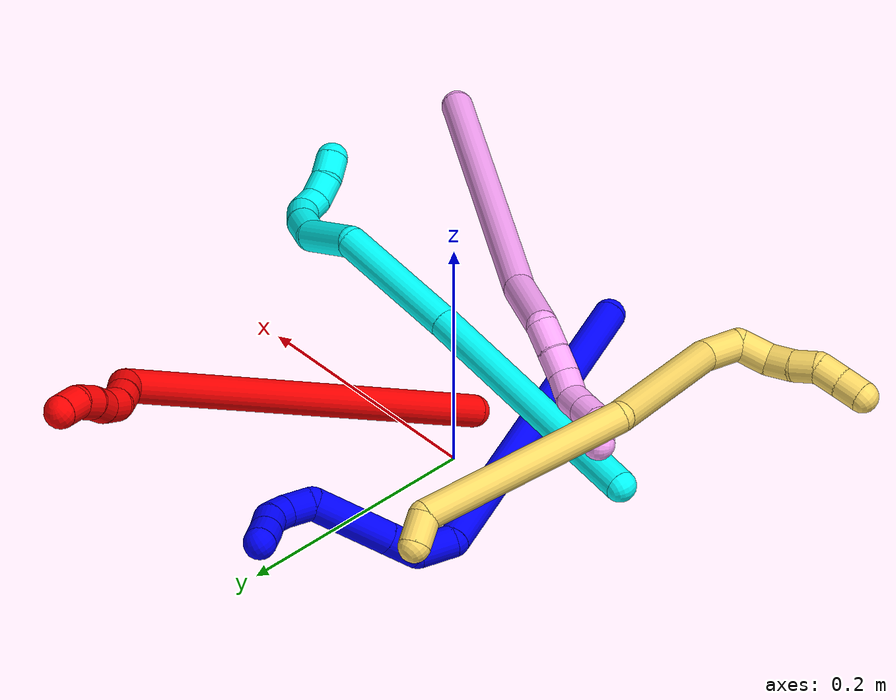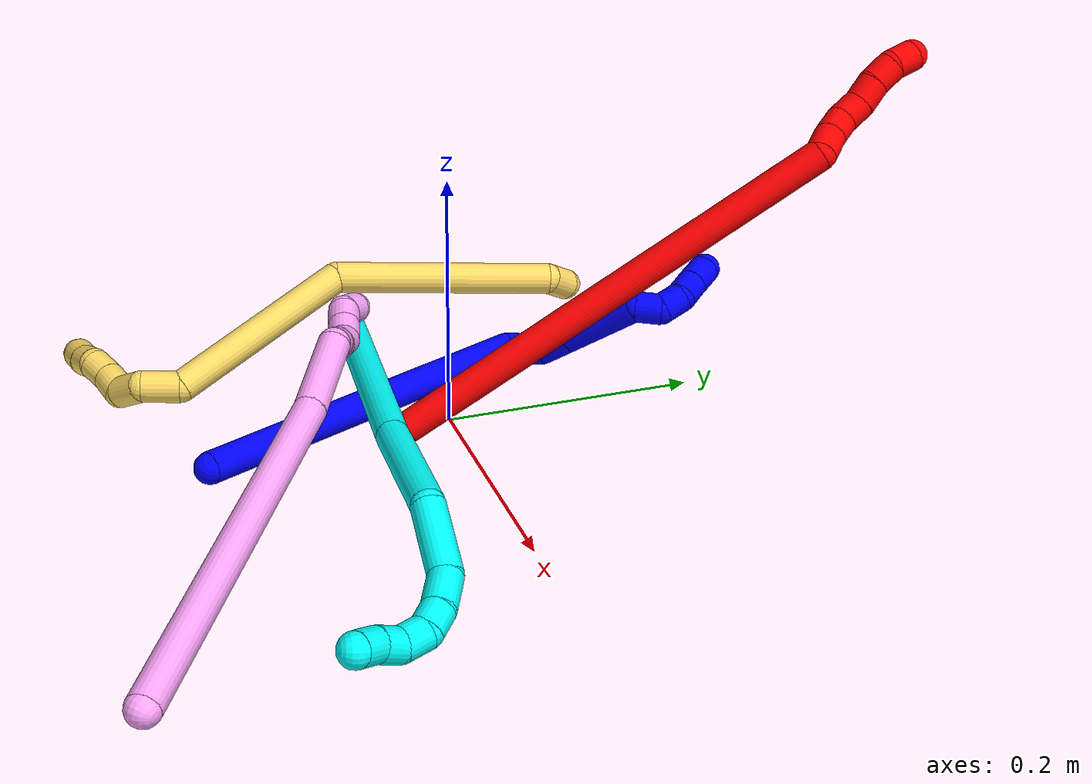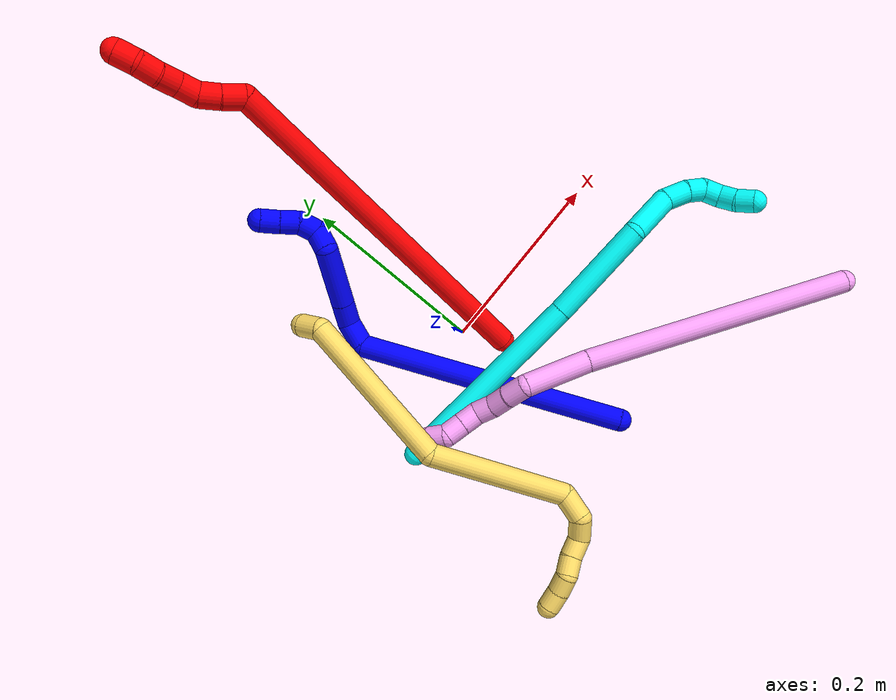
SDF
<sdf version="1.7">
 <world name="default">
  <plugin name="TubeGeneratorPlugin" filename="libtube_generator_plugin.so"/>
  <model name="photoneo_s_sensor">
   <static>1</static>
   <pose>0 0 2 1.57079 1.57079 3.14159</pose>
   <link name="link">
    <inertial><mass>0.1</mass></inertial>
    <sensor name="sensor" type="depth">
     <update_rate>30</update_rate>
     <camera>
      <horizontal_fov>1.22</horizontal_fov>
      <image><width>1920</width><height>1200</height><format>B8G8R8</format></image>
      <clip><near>0.1</near><far>4</far></clip>
      <depth_camera><output>points</output></depth_camera>
     </camera>
     <plugin name="camera_plugin" filename="libgazebo_ros_depth_camera.so">
      <baseline>0.2</baseline>
      <alwaysOn>1</alwaysOn>
      <updateRate>0.0</updateRate>
      <cameraName>camera_ir</cameraName>
      <imageTopicName>/camera/color/image_raw</imageTopicName>
      <cameraInfoTopicName>/camera/color/camera_info</cameraInfoTopicName>
      <depthImageTopicName>/camera/depth/image_raw</depthImageTopicName>
      <depthImageCameraInfoTopicName>/camera/depth/camera_info</depthImageCameraInfoTopicName>
      <pointCloudTopicName>/camera/depth/points</pointCloudTopicName>
      <frameName>fr_optical</frameName>
      <pointCloudCutoff>0.1</pointCloudCutoff>
      <pointCloudCutoffMax>2.0</pointCloudCutoffMax>
      <distortionK1>0</distortionK1>
      <distortionK2>0</distortionK2>
      <distortionK3>0</distortionK3>
      <distortionT1>0</distortionT1>
      <distortionT2>0</distortionT2>
      <CxPrime>0</CxPrime>
      <Cx>0</Cx>
      <Cy>0</Cy>
      <focalLength>0</focalLength>
      <hackBaseline>0</hackBaseline>
     </plugin>
    </sensor>
   </link>
  </model>
  <gravity>0 0 -9.8</gravity>
  <magnetic_field>6e-06 2.3e-05 -4.2e-05</magnetic_field>
  <atmosphere type="adiabatic"/>
  <physics name="default_physics" default="0" type="ode">
   <max_step_size>0.003</max_step_size>
   <real_time_factor>1</real_time_factor>
   <real_time_update_rate>1000</real_time_update_rate>
   <max_contacts>10000</max_contacts>
   <ode>
    <solver>
     <type>quick</type>
     <iters>100</iters>
     <sor>1.3</sor>
     <use_dynamic_moi_rescaling>0</use_dynamic_moi_rescaling>
    </solver>
    <constraints>
     <contact_max_correcting_vel>0</contact_max_correcting_vel>
     <contact_surface_layer>0.001</contact_surface_layer>
     <cfm>0</cfm>
     <erp>0.2</erp>
    </constraints>
   </ode>
  </physics>
  <scene><ambient>0.4 0.4 0.4 1</ambient><background>0.7 0.7 0.7 1</background><shadows>0</shadows></scene>
  <audio><device>default</device></audio>
  <spherical_coordinates>
   <surface_model>EARTH_WGS84</surface_model>
   <latitude_deg>0</latitude_deg>
   <longitude_deg>0</longitude_deg>
   <elevation>0</elevation>
   <heading_deg>0</heading_deg>
  </spherical_coordinates>
  <model name="bin">
   <static>1</static>
   <link name="bottom">
    <collision name="collision-bottom">
     <pose>0 0 -0.01 0 -0 0</pose>
     <geometry><box><size>0.8 0.6 0.02</size></box></geometry>
     <surface>
      <friction><ode><mu>100</mu><mu2>100</mu2></ode></friction>
      <contact><collide_bitmask>65535</collide_bitmask></contact>
     </surface>
    </collision>
   </link>
   <link name="west_wall">
    <collision name="collision-west_wall">
     <pose>-0.41 0 0.1 0 -0 0</pose>
     <geometry><box><size>0.02 0.6 0.2</size></box></geometry>
     <surface>
      <friction><ode><mu>100</mu><mu2>100</mu2></ode></friction>
      <contact><collide_bitmask>65535</collide_bitmask></contact>
     </surface>
    </collision>
   </link>
   <link name="east_wall">
    <collision name="collision-east_wall">
     <pose>0.41 0 0.1 0 -0 0</pose>
     <geometry><box><size>0.02 0.6 0.2</size></box></geometry>
     <surface>
      <friction><ode><mu>100</mu><mu2>100</mu2></ode></friction>
      <contact><collide_bitmask>65535</collide_bitmask></contact>
     </surface>
    </collision>
   </link>
   <link name="south_wall">
    <collision name="collision-south_wall">
     <pose>0 -0.31 0.1 0 -0 0</pose>
     <geometry><box><size>0.8 0.02 0.2</size></box></geometry>
     <surface>
      <friction><ode><mu>100</mu><mu2>100</mu2></ode></friction>
      <contact><collide_bitmask>65535</collide_bitmask></contact>
     </surface>
    </collision>
   </link>
   <link name="north_wall">
    <collision name="collision-north_wall">
     <pose>0 0.31 0.1 0 -0 0</pose>
     <geometry><box><size>0.8 0.02 0.2</size></box></geometry>
     <surface>
      <friction><ode><mu>100</mu><mu2>100</mu2></ode></friction>
      <contact><collide_bitmask>65535</collide_bitmask></contact>
     </surface>
    </collision>
   </link>
  </model>
  <model name="1">
   <static>0</static>
   <link name="1">
    <collision name="collision-cylinder-e_1_1_4">
     <pose>-0.057322 0.135422 -0.010485 -1.64807 -0.399344 0.43051</pose>
     <geometry><cylinder><radius>0.0125</radius><length>0.294855</length></cylinder></geometry>
     <surface>
      <friction><ode><mu>1.16</mu><mu2>1.16</mu2><slip1>0</slip1><slip2>0</slip2></ode></friction>
      <contact><ode><kp>1e+06</kp><kd>1</kd><max_vel>0</max_vel><min_depth>0.001</min_depth></ode></contact>
     </surface>
    </collision>
    <visual name="visual-cylinder-e_1_1_4">
     <pose>-0.057322 0.135422 -0.010485 -1.64807 -0.399344 0.43051</pose>
     <geometry><cylinder><radius>0.0125</radius><length>0.294855</length></cylinder></geometry>
     <material><ambient>0 0 1 1</ambient></material>
    </visual>
    <collision name="collision-cylinder-e_2_4_5">
     <pose>-0.111162 0.284147 -0.016579 -1.25201 0.243625 -0.17656</pose>
     <geometry><cylinder><radius>0.0125</radius><length>0.02887</length></cylinder></geometry>
     <surface>
      <friction><ode><mu>1.16</mu><mu2>1.16</mu2><slip1>0</slip1><slip2>0</slip2></ode></friction>
      <contact><ode><kp>1e+06</kp><kd>1</kd><max_vel>0</max_vel><min_depth>0.001</min_depth></ode></contact>
     </surface>
    </collision>
    <visual name="visual-cylinder-e_2_4_5">
     <pose>-0.111162 0.284147 -0.016579 -1.25201 0.243625 -0.17656</pose>
     <geometry><cylinder><radius>0.0125</radius><length>0.02887</length></cylinder></geometry>
     <material><ambient>0 0 1 1</ambient></material>
    </visual>
    <collision name="collision-cylinder-e_3_5_6">
     <pose>-0.106799 0.304572 -0.000535 -0.548557 0.064399 -0.018126</pose>
     <geometry><cylinder><radius>0.0125</radius><length>0.027372</length></cylinder></geometry>
     <surface>
      <friction><ode><mu>1.16</mu><mu2>1.16</mu2><slip1>0</slip1><slip2>0</slip2></ode></friction>
      <contact><ode><kp>1e+06</kp><kd>1</kd><max_vel>0</max_vel><min_depth>0.001</min_depth></ode></contact>
     </surface>
    </collision>
    <visual name="visual-cylinder-e_3_5_6">
     <pose>-0.106799 0.304572 -0.000535 -0.548557 0.064399 -0.018126</pose>
     <geometry><cylinder><radius>0.0125</radius><length>0.027372</length></cylinder></geometry>
     <material><ambient>0 0 1 1</ambient></material>
    </visual>
    <collision name="collision-cylinder-e_4_6_7">
     <pose>-0.103843 0.328982 0.039391 -0.548826 0.062552 -0.017615</pose>
     <geometry><cylinder><radius>0.0125</radius><length>0.06641</length></cylinder></geometry>
     <surface>
      <friction><ode><mu>1.16</mu><mu2>1.16</mu2><slip1>0</slip1><slip2>0</slip2></ode></friction>
      <contact><ode><kp>1e+06</kp><kd>1</kd><max_vel>0</max_vel><min_depth>0.001</min_depth></ode></contact>
     </surface>
    </collision>
    <visual name="visual-cylinder-e_4_6_7">
     <pose>-0.103843 0.328982 0.039391 -0.548826 0.062552 -0.017615</pose>
     <geometry><cylinder><radius>0.0125</radius><length>0.06641</length></cylinder></geometry>
     <material><ambient>0 0 1 1</ambient></material>
    </visual>
    <collision name="collision-cylinder-e_5_7_8">
     <pose>-0.098658 0.356031 0.070962 -1.24497 0.293077 -0.211064</pose>
     <geometry><cylinder><radius>0.0125</radius><length>0.021522</length></cylinder></geometry>
     <surface>
      <friction><ode><mu>1.16</mu><mu2>1.16</mu2><slip1>0</slip1><slip2>0</slip2></ode></friction>
      <contact><ode><kp>1e+06</kp><kd>1</kd><max_vel>0</max_vel><min_depth>0.001</min_depth></ode></contact>
     </surface>
    </collision>
    <visual name="visual-cylinder-e_5_7_8">
     <pose>-0.098658 0.356031 0.070962 -1.24497 0.293077 -0.211064</pose>
     <geometry><cylinder><radius>0.0125</radius><length>0.021522</length></cylinder></geometry>
     <material><ambient>0 0 1 1</ambient></material>
    </visual>
    <collision name="collision-cylinder-e_6_8_9">
     <pose>-0.099683 0.374528 0.077102 -1.25624 -0.422749 0.309186</pose>
     <geometry><cylinder><radius>0.0125</radius><length>0.020149</length></cylinder></geometry>
     <surface>
      <friction><ode><mu>1.16</mu><mu2>1.16</mu2><slip1>0</slip1><slip2>0</slip2></ode></friction>
      <contact><ode><kp>1e+06</kp><kd>1</kd><max_vel>0</max_vel><min_depth>0.001</min_depth></ode></contact>
     </surface>
    </collision>
    <visual name="visual-cylinder-e_6_8_9">
     <pose>-0.099683 0.374528 0.077102 -1.25624 -0.422749 0.309186</pose>
     <geometry><cylinder><radius>0.0125</radius><length>0.020149</length></cylinder></geometry>
     <material><ambient>0 0 1 1</ambient></material>
    </visual>
    <collision name="collision-cylinder-e_7_9_10">
     <pose>-0.110829 0.390524 0.079461 -1.63726 -0.767011 0.814278</pose>
     <geometry><cylinder><radius>0.0125</radius><length>0.02021</length></cylinder></geometry>
     <surface>
      <friction><ode><mu>1.16</mu><mu2>1.16</mu2><slip1>0</slip1><slip2>0</slip2></ode></friction>
      <contact><ode><kp>1e+06</kp><kd>1</kd><max_vel>0</max_vel><min_depth>0.001</min_depth></ode></contact>
     </surface>
    </collision>
    <visual name="visual-cylinder-e_7_9_10">
     <pose>-0.110829 0.390524 0.079461 -1.63726 -0.767011 0.814278</pose>
     <geometry><cylinder><radius>0.0125</radius><length>0.02021</length></cylinder></geometry>
     <material><ambient>0 0 1 1</ambient></material>
    </visual>
    <collision name="collision-cylinder-e_8_10_2">
     <pose>-0.124753 0.405428 0.079087 -1.55654 -0.734987 0.725476</pose>
     <geometry><cylinder><radius>0.0125</radius><length>0.020613</length></cylinder></geometry>
     <surface>
      <friction><ode><mu>1.16</mu><mu2>1.16</mu2><slip1>0</slip1><slip2>0</slip2></ode></friction>
      <contact><ode><kp>1e+06</kp><kd>1</kd><max_vel>0</max_vel><min_depth>0.001</min_depth></ode></contact>
     </surface>
    </collision>
    <visual name="visual-cylinder-e_8_10_2">
     <pose>-0.124753 0.405428 0.079087 -1.55654 -0.734987 0.725476</pose>
     <geometry><cylinder><radius>0.0125</radius><length>0.020613</length></cylinder></geometry>
     <material><ambient>0 0 1 1</ambient></material>
    </visual>
    <collision name="collision-sphere-2">
     <pose>-0.131664 0.413073 0.079196 0 -0 0</pose>
     <geometry><sphere><radius>0.0125</radius></sphere></geometry>
     <surface>
      <friction><ode><mu>1.16</mu><mu2>1.16</mu2><slip1>0</slip1><slip2>0</slip2></ode></friction>
      <contact><ode><kp>1e+06</kp><kd>1</kd><max_vel>0</max_vel><min_depth>0.001</min_depth></ode></contact>
     </surface>
    </collision>
    <visual name="visual-sphere-2">
     <pose>-0.131664 0.413073 0.079196 0 -0 0</pose>
     <geometry><sphere><radius>0.0125</radius></sphere></geometry>
     <material><ambient>0 0 1 1</ambient></material>
    </visual>
    <collision name="collision-sphere-10">
     <pose>-0.117842 0.397783 0.078978 0 -0 0</pose>
     <geometry><sphere><radius>0.0125</radius></sphere></geometry>
     <surface>
      <friction><ode><mu>1.16</mu><mu2>1.16</mu2><slip1>0</slip1><slip2>0</slip2></ode></friction>
      <contact><ode><kp>1e+06</kp><kd>1</kd><max_vel>0</max_vel><min_depth>0.001</min_depth></ode></contact>
     </surface>
    </collision>
    <visual name="visual-sphere-10">
     <pose>-0.117842 0.397783 0.078978 0 -0 0</pose>
     <geometry><sphere><radius>0.0125</radius></sphere></geometry>
     <material><ambient>0 0 1 1</ambient></material>
    </visual>
    <collision name="collision-sphere-9">
     <pose>-0.103816 0.383264 0.079945 0 -0 0</pose>
     <geometry><sphere><radius>0.0125</radius></sphere></geometry>
     <surface>
      <friction><ode><mu>1.16</mu><mu2>1.16</mu2><slip1>0</slip1><slip2>0</slip2></ode></friction>
      <contact><ode><kp>1e+06</kp><kd>1</kd><max_vel>0</max_vel><min_depth>0.001</min_depth></ode></contact>
     </surface>
    </collision>
    <visual name="visual-sphere-9">
     <pose>-0.103816 0.383264 0.079945 0 -0 0</pose>
     <geometry><sphere><radius>0.0125</radius></sphere></geometry>
     <material><ambient>0 0 1 1</ambient></material>
    </visual>
    <collision name="collision-sphere-4">
     <pose>-0.114644 0.270844 -0.02097 0 -0 0</pose>
     <geometry><sphere><radius>0.0125</radius></sphere></geometry>
     <surface>
      <friction><ode><mu>1.16</mu><mu2>1.16</mu2><slip1>0</slip1><slip2>0</slip2></ode></friction>
      <contact><ode><kp>1e+06</kp><kd>1</kd><max_vel>0</max_vel><min_depth>0.001</min_depth></ode></contact>
     </surface>
    </collision>
    <visual name="visual-sphere-4">
     <pose>-0.114644 0.270844 -0.02097 0 -0 0</pose>
     <geometry><sphere><radius>0.0125</radius></sphere></geometry>
     <material><ambient>0 0 1 1</ambient></material>
    </visual>
    <collision name="collision-sphere-1">
     <geometry><sphere><radius>0.0125</radius></sphere></geometry>
     <surface>
      <friction><ode><mu>1.16</mu><mu2>1.16</mu2><slip1>0</slip1><slip2>0</slip2></ode></friction>
      <contact><ode><kp>1e+06</kp><kd>1</kd><max_vel>0</max_vel><min_depth>0.001</min_depth></ode></contact>
     </surface>
    </collision>
    <visual name="visual-sphere-1">
     <geometry><sphere><radius>0.0125</radius></sphere></geometry>
     <material><ambient>0 0 1 1</ambient></material>
    </visual>
    <collision name="collision-sphere-8">
     <pose>-0.095549 0.365791 0.07426 0 -0 0</pose>
     <geometry><sphere><radius>0.0125</radius></sphere></geometry>
     <surface>
      <friction><ode><mu>1.16</mu><mu2>1.16</mu2><slip1>0</slip1><slip2>0</slip2></ode></friction>
      <contact><ode><kp>1e+06</kp><kd>1</kd><max_vel>0</max_vel><min_depth>0.001</min_depth></ode></contact>
     </surface>
    </collision>
    <visual name="visual-sphere-8">
     <pose>-0.095549 0.365791 0.07426 0 -0 0</pose>
     <geometry><sphere><radius>0.0125</radius></sphere></geometry>
     <material><ambient>0 0 1 1</ambient></material>
    </visual>
    <collision name="collision-sphere-5">
     <pose>-0.10768 0.29745 -0.012189 0 -0 0</pose>
     <geometry><sphere><radius>0.0125</radius></sphere></geometry>
     <surface>
      <friction><ode><mu>1.16</mu><mu2>1.16</mu2><slip1>0</slip1><slip2>0</slip2></ode></friction>
      <contact><ode><kp>1e+06</kp><kd>1</kd><max_vel>0</max_vel><min_depth>0.001</min_depth></ode></contact>
     </surface>
    </collision>
    <visual name="visual-sphere-5">
     <pose>-0.10768 0.29745 -0.012189 0 -0 0</pose>
     <geometry><sphere><radius>0.0125</radius></sphere></geometry>
     <material><ambient>0 0 1 1</ambient></material>
    </visual>
    <collision name="collision-sphere-6">
     <pose>-0.105918 0.311693 0.011119 0 -0 0</pose>
     <geometry><sphere><radius>0.0125</radius></sphere></geometry>
     <surface>
      <friction><ode><mu>1.16</mu><mu2>1.16</mu2><slip1>0</slip1><slip2>0</slip2></ode></friction>
      <contact><ode><kp>1e+06</kp><kd>1</kd><max_vel>0</max_vel><min_depth>0.001</min_depth></ode></contact>
     </surface>
    </collision>
    <visual name="visual-sphere-6">
     <pose>-0.105918 0.311693 0.011119 0 -0 0</pose>
     <geometry><sphere><radius>0.0125</radius></sphere></geometry>
     <material><ambient>0 0 1 1</ambient></material>
    </visual>
    <collision name="collision-sphere-7">
     <pose>-0.101767 0.346271 0.067664 0 -0 0</pose>
     <geometry><sphere><radius>0.0125</radius></sphere></geometry>
     <surface>
      <friction><ode><mu>1.16</mu><mu2>1.16</mu2><slip1>0</slip1><slip2>0</slip2></ode></friction>
      <contact><ode><kp>1e+06</kp><kd>1</kd><max_vel>0</max_vel><min_depth>0.001</min_depth></ode></contact>
     </surface>
    </collision>
    <visual name="visual-sphere-7">
     <pose>-0.101767 0.346271 0.067664 0 -0 0</pose>
     <geometry><sphere><radius>0.0125</radius></sphere></geometry>
     <material><ambient>0 0 1 1</ambient></material>
    </visual>
    <inertial>
     <pose>-0.077747 0.219551 0.010696 0 -0 0</pose>
     <mass>0.5</mass>
     <inertia>
      <ixx>0.002651</ixx>
      <ixy>0</ixy>
      <ixz>0</ixz>
      <iyy>0.001085</iyy>
      <iyz>0</iyz>
      <izz>-0.001155</izz>
     </inertia>
    </inertial>
   </link>
   <pose>0.036019 -0.195751 0.011494 -0.212114 0.605437 -0.082248</pose>
  </model>
  <model name="2">
   <static>0</static>
   <link name="2">
    <collision name="collision-cylinder-e_1_1_4">
     <pose>0.00734 0.089174 0.165847 -0.493341 0.038962 -0.009812</pose>
     <geometry><cylinder><radius>0.0125</radius><length>0.376887</length></cylinder></geometry>
     <surface>
      <friction><ode><mu>1.16</mu><mu2>1.16</mu2><slip1>0</slip1><slip2>0</slip2></ode></friction>
      <contact><ode><kp>1e+06</kp><kd>1</kd><max_vel>0</max_vel><min_depth>0.001</min_depth></ode></contact>
     </surface>
    </collision>
    <visual name="visual-cylinder-e_1_1_4">
     <pose>0.00734 0.089174 0.165847 -0.493341 0.038962 -0.009812</pose>
     <geometry><cylinder><radius>0.0125</radius><length>0.376887</length></cylinder></geometry>
     <material><ambient>1 0 0 1</ambient></material>
    </visual>
    <collision name="collision-cylinder-e_2_4_5">
     <pose>0.007195 0.182215 0.339098 -0.481405 -0.73062 0.187218</pose>
     <geometry><cylinder><radius>0.0125</radius><length>0.022434</length></cylinder></geometry>
     <surface>
      <friction><ode><mu>1.16</mu><mu2>1.16</mu2><slip1>0</slip1><slip2>0</slip2></ode></friction>
      <contact><ode><kp>1e+06</kp><kd>1</kd><max_vel>0</max_vel><min_depth>0.001</min_depth></ode></contact>
     </surface>
    </collision>
    <visual name="visual-cylinder-e_2_4_5">
     <pose>0.007195 0.182215 0.339098 -0.481405 -0.73062 0.187218</pose>
     <geometry><cylinder><radius>0.0125</radius><length>0.022434</length></cylinder></geometry>
     <material><ambient>1 0 0 1</ambient></material>
    </visual>
    <collision name="collision-cylinder-e_3_5_6">
     <pose>-0.006439 0.190559 0.353491 -0.569633 -0.63763 0.192678</pose>
     <geometry><cylinder><radius>0.0125</radius><length>0.020657</length></cylinder></geometry>
     <surface>
      <friction><ode><mu>1.16</mu><mu2>1.16</mu2><slip1>0</slip1><slip2>0</slip2></ode></friction>
      <contact><ode><kp>1e+06</kp><kd>1</kd><max_vel>0</max_vel><min_depth>0.001</min_depth></ode></contact>
     </surface>
    </collision>
    <visual name="visual-cylinder-e_3_5_6">
     <pose>-0.006439 0.190559 0.353491 -0.569633 -0.63763 0.192678</pose>
     <geometry><cylinder><radius>0.0125</radius><length>0.020657</length></cylinder></geometry>
     <material><ambient>1 0 0 1</ambient></material>
    </visual>
    <collision name="collision-cylinder-e_4_6_7">
     <pose>-0.014972 0.199538 0.369093 -0.48173 -0.240562 0.059359</pose>
     <geometry><cylinder><radius>0.0125</radius><length>0.020014</length></cylinder></geometry>
     <surface>
      <friction><ode><mu>1.16</mu><mu2>1.16</mu2><slip1>0</slip1><slip2>0</slip2></ode></friction>
      <contact><ode><kp>1e+06</kp><kd>1</kd><max_vel>0</max_vel><min_depth>0.001</min_depth></ode></contact>
     </surface>
    </collision>
    <visual name="visual-cylinder-e_4_6_7">
     <pose>-0.014972 0.199538 0.369093 -0.48173 -0.240562 0.059359</pose>
     <geometry><cylinder><radius>0.0125</radius><length>0.020014</length></cylinder></geometry>
     <material><ambient>1 0 0 1</ambient></material>
    </visual>
    <collision name="collision-cylinder-e_5_7_8">
     <pose>-0.019672 0.206099 0.387214 -0.213152 -0.233734 0.025118</pose>
     <geometry><cylinder><radius>0.0125</radius><length>0.020002</length></cylinder></geometry>
     <surface>
      <friction><ode><mu>1.16</mu><mu2>1.16</mu2><slip1>0</slip1><slip2>0</slip2></ode></friction>
      <contact><ode><kp>1e+06</kp><kd>1</kd><max_vel>0</max_vel><min_depth>0.001</min_depth></ode></contact>
     </surface>
    </collision>
    <visual name="visual-cylinder-e_5_7_8">
     <pose>-0.019672 0.206099 0.387214 -0.213152 -0.233734 0.025118</pose>
     <geometry><cylinder><radius>0.0125</radius><length>0.020002</length></cylinder></geometry>
     <material><ambient>1 0 0 1</ambient></material>
    </visual>
    <collision name="collision-cylinder-e_6_8_9">
     <pose>-0.023712 0.212126 0.405739 -0.414652 -0.173204 0.036521</pose>
     <geometry><cylinder><radius>0.0125</radius><length>0.020001</length></cylinder></geometry>
     <surface>
      <friction><ode><mu>1.16</mu><mu2>1.16</mu2><slip1>0</slip1><slip2>0</slip2></ode></friction>
      <contact><ode><kp>1e+06</kp><kd>1</kd><max_vel>0</max_vel><min_depth>0.001</min_depth></ode></contact>
     </surface>
    </collision>
    <visual name="visual-cylinder-e_6_8_9">
     <pose>-0.023712 0.212126 0.405739 -0.414652 -0.173204 0.036521</pose>
     <geometry><cylinder><radius>0.0125</radius><length>0.020001</length></cylinder></geometry>
     <material><ambient>1 0 0 1</ambient></material>
    </visual>
    <collision name="collision-cylinder-e_7_9_2">
     <pose>-0.028044 0.22291 0.421597 -0.78347 -0.263797 0.109497</pose>
     <geometry><cylinder><radius>0.0125</radius><length>0.020005</length></cylinder></geometry>
     <surface>
      <friction><ode><mu>1.16</mu><mu2>1.16</mu2><slip1>0</slip1><slip2>0</slip2></ode></friction>
      <contact><ode><kp>1e+06</kp><kd>1</kd><max_vel>0</max_vel><min_depth>0.001</min_depth></ode></contact>
     </surface>
    </collision>
    <visual name="visual-cylinder-e_7_9_2">
     <pose>-0.028044 0.22291 0.421597 -0.78347 -0.263797 0.109497</pose>
     <geometry><cylinder><radius>0.0125</radius><length>0.020005</length></cylinder></geometry>
     <material><ambient>1 0 0 1</ambient></material>
    </visual>
    <collision name="collision-sphere-2">
     <pose>-0.030652 0.229724 0.428438 0 -0 0</pose>
     <geometry><sphere><radius>0.0125</radius></sphere></geometry>
     <surface>
      <friction><ode><mu>1.16</mu><mu2>1.16</mu2><slip1>0</slip1><slip2>0</slip2></ode></friction>
      <contact><ode><kp>1e+06</kp><kd>1</kd><max_vel>0</max_vel><min_depth>0.001</min_depth></ode></contact>
     </surface>
    </collision>
    <visual name="visual-sphere-2">
     <pose>-0.030652 0.229724 0.428438 0 -0 0</pose>
     <geometry><sphere><radius>0.0125</radius></sphere></geometry>
     <material><ambient>1 0 0 1</ambient></material>
    </visual>
    <collision name="collision-sphere-9">
     <pose>-0.025436 0.216095 0.414755 0 -0 0</pose>
     <geometry><sphere><radius>0.0125</radius></sphere></geometry>
     <surface>
      <friction><ode><mu>1.16</mu><mu2>1.16</mu2><slip1>0</slip1><slip2>0</slip2></ode></friction>
      <contact><ode><kp>1e+06</kp><kd>1</kd><max_vel>0</max_vel><min_depth>0.001</min_depth></ode></contact>
     </surface>
    </collision>
    <visual name="visual-sphere-9">
     <pose>-0.025436 0.216095 0.414755 0 -0 0</pose>
     <geometry><sphere><radius>0.0125</radius></sphere></geometry>
     <material><ambient>1 0 0 1</ambient></material>
    </visual>
    <collision name="collision-sphere-4">
     <pose>0.014681 0.178347 0.331693 0 -0 0</pose>
     <geometry><sphere><radius>0.0125</radius></sphere></geometry>
     <surface>
      <friction><ode><mu>1.16</mu><mu2>1.16</mu2><slip1>0</slip1><slip2>0</slip2></ode></friction>
      <contact><ode><kp>1e+06</kp><kd>1</kd><max_vel>0</max_vel><min_depth>0.001</min_depth></ode></contact>
     </surface>
    </collision>
    <visual name="visual-sphere-4">
     <pose>0.014681 0.178347 0.331693 0 -0 0</pose>
     <geometry><sphere><radius>0.0125</radius></sphere></geometry>
     <material><ambient>1 0 0 1</ambient></material>
    </visual>
    <collision name="collision-sphere-1">
     <geometry><sphere><radius>0.0125</radius></sphere></geometry>
     <surface>
      <friction><ode><mu>1.16</mu><mu2>1.16</mu2><slip1>0</slip1><slip2>0</slip2></ode></friction>
      <contact><ode><kp>1e+06</kp><kd>1</kd><max_vel>0</max_vel><min_depth>0.001</min_depth></ode></contact>
     </surface>
    </collision>
    <visual name="visual-sphere-1">
     <geometry><sphere><radius>0.0125</radius></sphere></geometry>
     <material><ambient>1 0 0 1</ambient></material>
    </visual>
    <collision name="collision-sphere-8">
     <pose>-0.021989 0.208157 0.396723 0 -0 0</pose>
     <geometry><sphere><radius>0.0125</radius></sphere></geometry>
     <surface>
      <friction><ode><mu>1.16</mu><mu2>1.16</mu2><slip1>0</slip1><slip2>0</slip2></ode></friction>
      <contact><ode><kp>1e+06</kp><kd>1</kd><max_vel>0</max_vel><min_depth>0.001</min_depth></ode></contact>
     </surface>
    </collision>
    <visual name="visual-sphere-8">
     <pose>-0.021989 0.208157 0.396723 0 -0 0</pose>
     <geometry><sphere><radius>0.0125</radius></sphere></geometry>
     <material><ambient>1 0 0 1</ambient></material>
    </visual>
    <collision name="collision-sphere-5">
     <pose>-0.00029 0.186083 0.346502 0 -0 0</pose>
     <geometry><sphere><radius>0.0125</radius></sphere></geometry>
     <surface>
      <friction><ode><mu>1.16</mu><mu2>1.16</mu2><slip1>0</slip1><slip2>0</slip2></ode></friction>
      <contact><ode><kp>1e+06</kp><kd>1</kd><max_vel>0</max_vel><min_depth>0.001</min_depth></ode></contact>
     </surface>
    </collision>
    <visual name="visual-sphere-5">
     <pose>-0.00029 0.186083 0.346502 0 -0 0</pose>
     <geometry><sphere><radius>0.0125</radius></sphere></geometry>
     <material><ambient>1 0 0 1</ambient></material>
    </visual>
    <collision name="collision-sphere-6">
     <pose>-0.012588 0.195035 0.36048 0 -0 0</pose>
     <geometry><sphere><radius>0.0125</radius></sphere></geometry>
     <surface>
      <friction><ode><mu>1.16</mu><mu2>1.16</mu2><slip1>0</slip1><slip2>0</slip2></ode></friction>
      <contact><ode><kp>1e+06</kp><kd>1</kd><max_vel>0</max_vel><min_depth>0.001</min_depth></ode></contact>
     </surface>
    </collision>
    <visual name="visual-sphere-6">
     <pose>-0.012588 0.195035 0.36048 0 -0 0</pose>
     <geometry><sphere><radius>0.0125</radius></sphere></geometry>
     <material><ambient>1 0 0 1</ambient></material>
    </visual>
    <collision name="collision-sphere-7">
     <pose>-0.017356 0.204041 0.377706 0 -0 0</pose>
     <geometry><sphere><radius>0.0125</radius></sphere></geometry>
     <surface>
      <friction><ode><mu>1.16</mu><mu2>1.16</mu2><slip1>0</slip1><slip2>0</slip2></ode></friction>
      <contact><ode><kp>1e+06</kp><kd>1</kd><max_vel>0</max_vel><min_depth>0.001</min_depth></ode></contact>
     </surface>
    </collision>
    <visual name="visual-sphere-7">
     <pose>-0.017356 0.204041 0.377706 0 -0 0</pose>
     <geometry><sphere><radius>0.0125</radius></sphere></geometry>
     <material><ambient>1 0 0 1</ambient></material>
    </visual>
    <inertial>
     <pose>0.002133 0.116901 0.218192 0 -0 0</pose>
     <mass>0.5</mass>
     <inertia>
      <ixx>0.004435</ixx>
      <ixy>0</ixy>
      <ixz>0</ixz>
      <iyy>0.003926</iyy>
      <iyz>0</iyz>
      <izz>-0.002259</izz>
     </inertia>
    </inertial>
   </link>
   <pose>0.02202 -0.039996 0.011493 -0.542276 -0.024245 -0.036453</pose>
  </model>
  <model name="3">
   <static>0</static>
   <link name="3">
    <collision name="collision-cylinder-e_1_1_4">
     <pose>0.109818 -0.007291 0.001896 1.31635 1.50231 1.25063</pose>
     <geometry><cylinder><radius>0.0125</radius><length>0.220152</length></cylinder></geometry>
     <surface>
      <friction><ode><mu>1.16</mu><mu2>1.16</mu2><slip1>0</slip1><slip2>0</slip2></ode></friction>
      <contact><ode><kp>1e+06</kp><kd>1</kd><max_vel>0</max_vel><min_depth>0.001</min_depth></ode></contact>
     </surface>
    </collision>
    <visual name="visual-cylinder-e_1_1_4">
     <pose>0.109818 -0.007291 0.001896 1.31635 1.50231 1.25063</pose>
     <geometry><cylinder><radius>0.0125</radius><length>0.220152</length></cylinder></geometry>
     <material><ambient>0.003922 1 0.996078 1</ambient></material>
    </visual>
    <collision name="collision-cylinder-e_2_4_5">
     <pose>0.277168 -0.017195 0.002447 2.04603 1.51974 2.00009</pose>
     <geometry><cylinder><radius>0.0125</radius><length>0.115214</length></cylinder></geometry>
     <surface>
      <friction><ode><mu>1.16</mu><mu2>1.16</mu2><slip1>0</slip1><slip2>0</slip2></ode></friction>
      <contact><ode><kp>1e+06</kp><kd>1</kd><max_vel>0</max_vel><min_depth>0.001</min_depth></ode></contact>
     </surface>
    </collision>
    <visual name="visual-cylinder-e_2_4_5">
     <pose>0.277168 -0.017195 0.002447 2.04603 1.51974 2.00009</pose>
     <geometry><cylinder><radius>0.0125</radius><length>0.115214</length></cylinder></geometry>
     <material><ambient>0.003922 1 0.996078 1</ambient></material>
    </visual>
    <collision name="collision-cylinder-e_3_5_6">
     <pose>0.358041 -0.034934 -0.001292 1.72779 0.990184 1.12744</pose>
     <geometry><cylinder><radius>0.0125</radius><length>0.055833</length></cylinder></geometry>
     <surface>
      <friction><ode><mu>1.16</mu><mu2>1.16</mu2><slip1>0</slip1><slip2>0</slip2></ode></friction>
      <contact><ode><kp>1e+06</kp><kd>1</kd><max_vel>0</max_vel><min_depth>0.001</min_depth></ode></contact>
     </surface>
    </collision>
    <visual name="visual-cylinder-e_3_5_6">
     <pose>0.358041 -0.034934 -0.001292 1.72779 0.990184 1.12744</pose>
     <geometry><cylinder><radius>0.0125</radius><length>0.055833</length></cylinder></geometry>
     <material><ambient>0.003922 1 0.996078 1</ambient></material>
    </visual>
    <collision name="collision-cylinder-e_4_6_7">
     <pose>0.393406 -0.056171 0.000899 0.927175 1.00463 0.536018</pose>
     <geometry><cylinder><radius>0.0125</radius><length>0.028491</length></cylinder></geometry>
     <surface>
      <friction><ode><mu>1.16</mu><mu2>1.16</mu2><slip1>0</slip1><slip2>0</slip2></ode></friction>
      <contact><ode><kp>1e+06</kp><kd>1</kd><max_vel>0</max_vel><min_depth>0.001</min_depth></ode></contact>
     </surface>
    </collision>
    <visual name="visual-cylinder-e_4_6_7">
     <pose>0.393406 -0.056171 0.000899 0.927175 1.00463 0.536018</pose>
     <geometry><cylinder><radius>0.0125</radius><length>0.028491</length></cylinder></geometry>
     <material><ambient>0.003922 1 0.996078 1</ambient></material>
    </visual>
    <collision name="collision-cylinder-e_5_7_8">
     <pose>0.412762 -0.066414 0.01093 0.648927 0.820655 0.290577</pose>
     <geometry><cylinder><radius>0.0125</radius><length>0.020049</length></cylinder></geometry>
     <surface>
      <friction><ode><mu>1.16</mu><mu2>1.16</mu2><slip1>0</slip1><slip2>0</slip2></ode></friction>
      <contact><ode><kp>1e+06</kp><kd>1</kd><max_vel>0</max_vel><min_depth>0.001</min_depth></ode></contact>
     </surface>
    </collision>
    <visual name="visual-cylinder-e_5_7_8">
     <pose>0.412762 -0.066414 0.01093 0.648927 0.820655 0.290577</pose>
     <geometry><cylinder><radius>0.0125</radius><length>0.020049</length></cylinder></geometry>
     <material><ambient>0.003922 1 0.996078 1</ambient></material>
    </visual>
    <collision name="collision-cylinder-e_6_8_9">
     <pose>0.423899 -0.073229 0.025305 0.292025 0.387181 0.057645</pose>
     <geometry><cylinder><radius>0.0125</radius><length>0.02014</length></cylinder></geometry>
     <surface>
      <friction><ode><mu>1.16</mu><mu2>1.16</mu2><slip1>0</slip1><slip2>0</slip2></ode></friction>
      <contact><ode><kp>1e+06</kp><kd>1</kd><max_vel>0</max_vel><min_depth>0.001</min_depth></ode></contact>
     </surface>
    </collision>
    <visual name="visual-cylinder-e_6_8_9">
     <pose>0.423899 -0.073229 0.025305 0.292025 0.387181 0.057645</pose>
     <geometry><cylinder><radius>0.0125</radius><length>0.02014</length></cylinder></geometry>
     <material><ambient>0.003922 1 0.996078 1</ambient></material>
    </visual>
    <collision name="collision-cylinder-e_7_9_10">
     <pose>0.431949 -0.07311 0.042871 -0.313909 0.437647 -0.070358</pose>
     <geometry><cylinder><radius>0.0125</radius><length>0.020048</length></cylinder></geometry>
     <surface>
      <friction><ode><mu>1.16</mu><mu2>1.16</mu2><slip1>0</slip1><slip2>0</slip2></ode></friction>
      <contact><ode><kp>1e+06</kp><kd>1</kd><max_vel>0</max_vel><min_depth>0.001</min_depth></ode></contact>
     </surface>
    </collision>
    <visual name="visual-cylinder-e_7_9_10">
     <pose>0.431949 -0.07311 0.042871 -0.313909 0.437647 -0.070358</pose>
     <geometry><cylinder><radius>0.0125</radius><length>0.020048</length></cylinder></geometry>
     <material><ambient>0.003922 1 0.996078 1</ambient></material>
    </visual>
    <collision name="collision-cylinder-e_8_10_2">
     <pose>0.442472 -0.068752 0.059183 -0.199793 0.675414 -0.070364</pose>
     <geometry><cylinder><radius>0.0125</radius><length>0.020073</length></cylinder></geometry>
     <surface>
      <friction><ode><mu>1.16</mu><mu2>1.16</mu2><slip1>0</slip1><slip2>0</slip2></ode></friction>
      <contact><ode><kp>1e+06</kp><kd>1</kd><max_vel>0</max_vel><min_depth>0.001</min_depth></ode></contact>
     </surface>
    </collision>
    <visual name="visual-cylinder-e_8_10_2">
     <pose>0.442472 -0.068752 0.059183 -0.199793 0.675414 -0.070364</pose>
     <geometry><cylinder><radius>0.0125</radius><length>0.020073</length></cylinder></geometry>
     <material><ambient>0.003922 1 0.996078 1</ambient></material>
    </visual>
    <collision name="collision-sphere-2">
     <pose>0.448747 -0.067197 0.06686 0 -0 0</pose>
     <geometry><sphere><radius>0.0125</radius></sphere></geometry>
     <surface>
      <friction><ode><mu>1.16</mu><mu2>1.16</mu2><slip1>0</slip1><slip2>0</slip2></ode></friction>
      <contact><ode><kp>1e+06</kp><kd>1</kd><max_vel>0</max_vel><min_depth>0.001</min_depth></ode></contact>
     </surface>
    </collision>
    <visual name="visual-sphere-2">
     <pose>0.448747 -0.067197 0.06686 0 -0 0</pose>
     <geometry><sphere><radius>0.0125</radius></sphere></geometry>
     <material><ambient>0.003922 1 0.996078 1</ambient></material>
    </visual>
    <collision name="collision-sphere-10">
     <pose>0.436197 -0.070306 0.051506 0 -0 0</pose>
     <geometry><sphere><radius>0.0125</radius></sphere></geometry>
     <surface>
      <friction><ode><mu>1.16</mu><mu2>1.16</mu2><slip1>0</slip1><slip2>0</slip2></ode></friction>
      <contact><ode><kp>1e+06</kp><kd>1</kd><max_vel>0</max_vel><min_depth>0.001</min_depth></ode></contact>
     </surface>
    </collision>
    <visual name="visual-sphere-10">
     <pose>0.436197 -0.070306 0.051506 0 -0 0</pose>
     <geometry><sphere><radius>0.0125</radius></sphere></geometry>
     <material><ambient>0.003922 1 0.996078 1</ambient></material>
    </visual>
    <collision name="collision-sphere-9">
     <pose>0.427701 -0.075913 0.034235 0 -0 0</pose>
     <geometry><sphere><radius>0.0125</radius></sphere></geometry>
     <surface>
      <friction><ode><mu>1.16</mu><mu2>1.16</mu2><slip1>0</slip1><slip2>0</slip2></ode></friction>
      <contact><ode><kp>1e+06</kp><kd>1</kd><max_vel>0</max_vel><min_depth>0.001</min_depth></ode></contact>
     </surface>
    </collision>
    <visual name="visual-sphere-9">
     <pose>0.427701 -0.075913 0.034235 0 -0 0</pose>
     <geometry><sphere><radius>0.0125</radius></sphere></geometry>
     <material><ambient>0.003922 1 0.996078 1</ambient></material>
    </visual>
    <collision name="collision-sphere-4">
     <pose>0.219636 -0.014581 0.003792 0 -0 0</pose>
     <geometry><sphere><radius>0.0125</radius></sphere></geometry>
     <surface>
      <friction><ode><mu>1.16</mu><mu2>1.16</mu2><slip1>0</slip1><slip2>0</slip2></ode></friction>
      <contact><ode><kp>1e+06</kp><kd>1</kd><max_vel>0</max_vel><min_depth>0.001</min_depth></ode></contact>
     </surface>
    </collision>
    <visual name="visual-sphere-4">
     <pose>0.219636 -0.014581 0.003792 0 -0 0</pose>
     <geometry><sphere><radius>0.0125</radius></sphere></geometry>
     <material><ambient>0.003922 1 0.996078 1</ambient></material>
    </visual>
    <collision name="collision-sphere-1">
     <geometry><sphere><radius>0.0125</radius></sphere></geometry>
     <surface>
      <friction><ode><mu>1.16</mu><mu2>1.16</mu2><slip1>0</slip1><slip2>0</slip2></ode></friction>
      <contact><ode><kp>1e+06</kp><kd>1</kd><max_vel>0</max_vel><min_depth>0.001</min_depth></ode></contact>
     </surface>
    </collision>
    <visual name="visual-sphere-1">
     <geometry><sphere><radius>0.0125</radius></sphere></geometry>
     <material><ambient>0.003922 1 0.996078 1</ambient></material>
    </visual>
    <collision name="collision-sphere-8">
     <pose>0.420096 -0.070544 0.016375 0 -0 0</pose>
     <geometry><sphere><radius>0.0125</radius></sphere></geometry>
     <surface>
      <friction><ode><mu>1.16</mu><mu2>1.16</mu2><slip1>0</slip1><slip2>0</slip2></ode></friction>
      <contact><ode><kp>1e+06</kp><kd>1</kd><max_vel>0</max_vel><min_depth>0.001</min_depth></ode></contact>
     </surface>
    </collision>
    <visual name="visual-sphere-8">
     <pose>0.420096 -0.070544 0.016375 0 -0 0</pose>
     <geometry><sphere><radius>0.0125</radius></sphere></geometry>
     <material><ambient>0.003922 1 0.996078 1</ambient></material>
    </visual>
    <collision name="collision-sphere-5">
     <pose>0.3347 -0.019809 0.001102 0 -0 0</pose>
     <geometry><sphere><radius>0.0125</radius></sphere></geometry>
     <surface>
      <friction><ode><mu>1.16</mu><mu2>1.16</mu2><slip1>0</slip1><slip2>0</slip2></ode></friction>
      <contact><ode><kp>1e+06</kp><kd>1</kd><max_vel>0</max_vel><min_depth>0.001</min_depth></ode></contact>
     </surface>
    </collision>
    <visual name="visual-sphere-5">
     <pose>0.3347 -0.019809 0.001102 0 -0 0</pose>
     <geometry><sphere><radius>0.0125</radius></sphere></geometry>
     <material><ambient>0.003922 1 0.996078 1</ambient></material>
    </visual>
    <collision name="collision-sphere-6">
     <pose>0.381383 -0.050059 -0.003686 0 -0 0</pose>
     <geometry><sphere><radius>0.0125</radius></sphere></geometry>
     <surface>
      <friction><ode><mu>1.16</mu><mu2>1.16</mu2><slip1>0</slip1><slip2>0</slip2></ode></friction>
      <contact><ode><kp>1e+06</kp><kd>1</kd><max_vel>0</max_vel><min_depth>0.001</min_depth></ode></contact>
     </surface>
    </collision>
    <visual name="visual-sphere-6">
     <pose>0.381383 -0.050059 -0.003686 0 -0 0</pose>
     <geometry><sphere><radius>0.0125</radius></sphere></geometry>
     <material><ambient>0.003922 1 0.996078 1</ambient></material>
    </visual>
    <collision name="collision-sphere-7">
     <pose>0.405428 -0.062284 0.005485 0 -0 0</pose>
     <geometry><sphere><radius>0.0125</radius></sphere></geometry>
     <surface>
      <friction><ode><mu>1.16</mu><mu2>1.16</mu2><slip1>0</slip1><slip2>0</slip2></ode></friction>
      <contact><ode><kp>1e+06</kp><kd>1</kd><max_vel>0</max_vel><min_depth>0.001</min_depth></ode></contact>
     </surface>
    </collision>
    <visual name="visual-sphere-7">
     <pose>0.405428 -0.062284 0.005485 0 -0 0</pose>
     <geometry><sphere><radius>0.0125</radius></sphere></geometry>
     <material><ambient>0.003922 1 0.996078 1</ambient></material>
    </visual>
    <inertial>
     <pose>0.243327 -0.025578 0.006858 0 -0 0</pose>
     <mass>0.5</mass>
     <inertia>
      <ixx>0.000135</ixx>
      <ixy>0</ixy>
      <ixz>0</ixz>
      <iyy>0.001114</iyy>
      <iyz>0</iyz>
      <izz>-0.000966</izz>
     </inertia>
    </inertial>
   </link>
   <pose>-0.13292 -0.046187 0.029423 1.44852 -0.126014 -0.079773</pose>
  </model>
  <model name="4">
   <static>0</static>
   <link name="4">
    <collision name="collision-cylinder-e_1_1_4">
     <pose>-0.122838 0.059366 -0.06466 -2.39885 -0.950341 1.84572</pose>
     <geometry><cylinder><radius>0.0125</radius><length>0.301956</length></cylinder></geometry>
     <surface>
      <friction><ode><mu>1.16</mu><mu2>1.16</mu2><slip1>0</slip1><slip2>0</slip2></ode></friction>
      <contact><ode><kp>1e+06</kp><kd>1</kd><max_vel>0</max_vel><min_depth>0.001</min_depth></ode></contact>
     </surface>
    </collision>
    <visual name="visual-cylinder-e_1_1_4">
     <pose>-0.122838 0.059366 -0.06466 -2.39885 -0.950341 1.84572</pose>
     <geometry><cylinder><radius>0.0125</radius><length>0.301956</length></cylinder></geometry>
     <material><ambient>1 0.65098 0.996078 1</ambient></material>
    </visual>
    <collision name="collision-cylinder-e_2_4_5">
     <pose>-0.275689 0.128817 -0.146981 -2.62279 -0.97524 2.21366</pose>
     <geometry><cylinder><radius>0.0125</radius><length>0.07251</length></cylinder></geometry>
     <surface>
      <friction><ode><mu>1.16</mu><mu2>1.16</mu2><slip1>0</slip1><slip2>0</slip2></ode></friction>
      <contact><ode><kp>1e+06</kp><kd>1</kd><max_vel>0</max_vel><min_depth>0.001</min_depth></ode></contact>
     </surface>
    </collision>
    <visual name="visual-cylinder-e_2_4_5">
     <pose>-0.275689 0.128817 -0.146981 -2.62279 -0.97524 2.21366</pose>
     <geometry><cylinder><radius>0.0125</radius><length>0.07251</length></cylinder></geometry>
     <material><ambient>1 0.65098 0.996078 1</ambient></material>
    </visual>
    <collision name="collision-cylinder-e_3_5_6">
     <pose>-0.309536 0.147906 -0.171444 -2.21771 -0.327499 0.640868</pose>
     <geometry><cylinder><radius>0.0125</radius><length>0.023836</length></cylinder></geometry>
     <surface>
      <friction><ode><mu>1.16</mu><mu2>1.16</mu2><slip1>0</slip1><slip2>0</slip2></ode></friction>
      <contact><ode><kp>1e+06</kp><kd>1</kd><max_vel>0</max_vel><min_depth>0.001</min_depth></ode></contact>
     </surface>
    </collision>
    <visual name="visual-cylinder-e_3_5_6">
     <pose>-0.309536 0.147906 -0.171444 -2.21771 -0.327499 0.640868</pose>
     <geometry><cylinder><radius>0.0125</radius><length>0.023836</length></cylinder></geometry>
     <material><ambient>1 0.65098 0.996078 1</ambient></material>
    </visual>
    <collision name="collision-cylinder-e_4_6_7">
     <pose>-0.315818 0.165169 -0.184183 -2.19414 -0.236255 0.454981</pose>
     <geometry><cylinder><radius>0.0125</radius><length>0.020924</length></cylinder></geometry>
     <surface>
      <friction><ode><mu>1.16</mu><mu2>1.16</mu2><slip1>0</slip1><slip2>0</slip2></ode></friction>
      <contact><ode><kp>1e+06</kp><kd>1</kd><max_vel>0</max_vel><min_depth>0.001</min_depth></ode></contact>
     </surface>
    </collision>
    <visual name="visual-cylinder-e_4_6_7">
     <pose>-0.315818 0.165169 -0.184183 -2.19414 -0.236255 0.454981</pose>
     <geometry><cylinder><radius>0.0125</radius><length>0.020924</length></cylinder></geometry>
     <material><ambient>1 0.65098 0.996078 1</ambient></material>
    </visual>
    <collision name="collision-cylinder-e_5_7_8">
     <pose>-0.323134 0.180646 -0.195274 -2.19074 -0.501943 0.924092</pose>
     <geometry><cylinder><radius>0.0125</radius><length>0.020234</length></cylinder></geometry>
     <surface>
      <friction><ode><mu>1.16</mu><mu2>1.16</mu2><slip1>0</slip1><slip2>0</slip2></ode></friction>
      <contact><ode><kp>1e+06</kp><kd>1</kd><max_vel>0</max_vel><min_depth>0.001</min_depth></ode></contact>
     </surface>
    </collision>
    <visual name="visual-cylinder-e_5_7_8">
     <pose>-0.323134 0.180646 -0.195274 -2.19074 -0.501943 0.924092</pose>
     <geometry><cylinder><radius>0.0125</radius><length>0.020234</length></cylinder></geometry>
     <material><ambient>1 0.65098 0.996078 1</ambient></material>
    </visual>
    <collision name="collision-cylinder-e_6_8_9">
     <pose>-0.334605 0.190918 -0.207438 -2.73087 -0.712214 2.12063</pose>
     <geometry><cylinder><radius>0.0125</radius><length>0.020207</length></cylinder></geometry>
     <surface>
      <friction><ode><mu>1.16</mu><mu2>1.16</mu2><slip1>0</slip1><slip2>0</slip2></ode></friction>
      <contact><ode><kp>1e+06</kp><kd>1</kd><max_vel>0</max_vel><min_depth>0.001</min_depth></ode></contact>
     </surface>
    </collision>
    <visual name="visual-cylinder-e_6_8_9">
     <pose>-0.334605 0.190918 -0.207438 -2.73087 -0.712214 2.12063</pose>
     <geometry><cylinder><radius>0.0125</radius><length>0.020207</length></cylinder></geometry>
     <material><ambient>1 0.65098 0.996078 1</ambient></material>
    </visual>
    <collision name="collision-cylinder-e_7_9_10">
     <pose>-0.347812 0.196917 -0.221492 -2.74551 -0.713292 2.15349</pose>
     <geometry><cylinder><radius>0.0125</radius><length>0.020187</length></cylinder></geometry>
     <surface>
      <friction><ode><mu>1.16</mu><mu2>1.16</mu2><slip1>0</slip1><slip2>0</slip2></ode></friction>
      <contact><ode><kp>1e+06</kp><kd>1</kd><max_vel>0</max_vel><min_depth>0.001</min_depth></ode></contact>
     </surface>
    </collision>
    <visual name="visual-cylinder-e_7_9_10">
     <pose>-0.347812 0.196917 -0.221492 -2.74551 -0.713292 2.15349</pose>
     <geometry><cylinder><radius>0.0125</radius><length>0.020187</length></cylinder></geometry>
     <material><ambient>1 0.65098 0.996078 1</ambient></material>
    </visual>
    <collision name="collision-cylinder-e_8_10_2">
     <pose>-0.360151 0.207618 -0.231433 -1.92857 -0.605682 0.846351</pose>
     <geometry><cylinder><radius>0.0125</radius><length>0.020146</length></cylinder></geometry>
     <surface>
      <friction><ode><mu>1.16</mu><mu2>1.16</mu2><slip1>0</slip1><slip2>0</slip2></ode></friction>
      <contact><ode><kp>1e+06</kp><kd>1</kd><max_vel>0</max_vel><min_depth>0.001</min_depth></ode></contact>
     </surface>
    </collision>
    <visual name="visual-cylinder-e_8_10_2">
     <pose>-0.360151 0.207618 -0.231433 -1.92857 -0.605682 0.846351</pose>
     <geometry><cylinder><radius>0.0125</radius><length>0.020146</length></cylinder></geometry>
     <material><ambient>1 0.65098 0.996078 1</ambient></material>
    </visual>
    <collision name="collision-sphere-2">
     <pose>-0.365886 0.215375 -0.234333 0 -0 0</pose>
     <geometry><sphere><radius>0.0125</radius></sphere></geometry>
     <surface>
      <friction><ode><mu>1.16</mu><mu2>1.16</mu2><slip1>0</slip1><slip2>0</slip2></ode></friction>
      <contact><ode><kp>1e+06</kp><kd>1</kd><max_vel>0</max_vel><min_depth>0.001</min_depth></ode></contact>
     </surface>
    </collision>
    <visual name="visual-sphere-2">
     <pose>-0.365886 0.215375 -0.234333 0 -0 0</pose>
     <geometry><sphere><radius>0.0125</radius></sphere></geometry>
     <material><ambient>1 0.65098 0.996078 1</ambient></material>
    </visual>
    <collision name="collision-sphere-10">
     <pose>-0.354416 0.199861 -0.228533 0 -0 0</pose>
     <geometry><sphere><radius>0.0125</radius></sphere></geometry>
     <surface>
      <friction><ode><mu>1.16</mu><mu2>1.16</mu2><slip1>0</slip1><slip2>0</slip2></ode></friction>
      <contact><ode><kp>1e+06</kp><kd>1</kd><max_vel>0</max_vel><min_depth>0.001</min_depth></ode></contact>
     </surface>
    </collision>
    <visual name="visual-sphere-10">
     <pose>-0.354416 0.199861 -0.228533 0 -0 0</pose>
     <geometry><sphere><radius>0.0125</radius></sphere></geometry>
     <material><ambient>1 0.65098 0.996078 1</ambient></material>
    </visual>
    <collision name="collision-sphere-9">
     <pose>-0.341208 0.193972 -0.21445 0 -0 0</pose>
     <geometry><sphere><radius>0.0125</radius></sphere></geometry>
     <surface>
      <friction><ode><mu>1.16</mu><mu2>1.16</mu2><slip1>0</slip1><slip2>0</slip2></ode></friction>
      <contact><ode><kp>1e+06</kp><kd>1</kd><max_vel>0</max_vel><min_depth>0.001</min_depth></ode></contact>
     </surface>
    </collision>
    <visual name="visual-sphere-9">
     <pose>-0.341208 0.193972 -0.21445 0 -0 0</pose>
     <geometry><sphere><radius>0.0125</radius></sphere></geometry>
     <material><ambient>1 0.65098 0.996078 1</ambient></material>
    </visual>
    <collision name="collision-sphere-4">
     <pose>-0.245676 0.118733 -0.129319 0 -0 0</pose>
     <geometry><sphere><radius>0.0125</radius></sphere></geometry>
     <surface>
      <friction><ode><mu>1.16</mu><mu2>1.16</mu2><slip1>0</slip1><slip2>0</slip2></ode></friction>
      <contact><ode><kp>1e+06</kp><kd>1</kd><max_vel>0</max_vel><min_depth>0.001</min_depth></ode></contact>
     </surface>
    </collision>
    <visual name="visual-sphere-4">
     <pose>-0.245676 0.118733 -0.129319 0 -0 0</pose>
     <geometry><sphere><radius>0.0125</radius></sphere></geometry>
     <material><ambient>1 0.65098 0.996078 1</ambient></material>
    </visual>
    <collision name="collision-sphere-1">
     <geometry><sphere><radius>0.0125</radius></sphere></geometry>
     <surface>
      <friction><ode><mu>1.16</mu><mu2>1.16</mu2><slip1>0</slip1><slip2>0</slip2></ode></friction>
      <contact><ode><kp>1e+06</kp><kd>1</kd><max_vel>0</max_vel><min_depth>0.001</min_depth></ode></contact>
     </surface>
    </collision>
    <visual name="visual-sphere-1">
     <geometry><sphere><radius>0.0125</radius></sphere></geometry>
     <material><ambient>1 0.65098 0.996078 1</ambient></material>
    </visual>
    <collision name="collision-sphere-8">
     <pose>-0.328002 0.187865 -0.200427 0 -0 0</pose>
     <geometry><sphere><radius>0.0125</radius></sphere></geometry>
     <surface>
      <friction><ode><mu>1.16</mu><mu2>1.16</mu2><slip1>0</slip1><slip2>0</slip2></ode></friction>
      <contact><ode><kp>1e+06</kp><kd>1</kd><max_vel>0</max_vel><min_depth>0.001</min_depth></ode></contact>
     </surface>
    </collision>
    <visual name="visual-sphere-8">
     <pose>-0.328002 0.187865 -0.200427 0 -0 0</pose>
     <geometry><sphere><radius>0.0125</radius></sphere></geometry>
     <material><ambient>1 0.65098 0.996078 1</ambient></material>
    </visual>
    <collision name="collision-sphere-5">
     <pose>-0.305702 0.138902 -0.164643 0 -0 0</pose>
     <geometry><sphere><radius>0.0125</radius></sphere></geometry>
     <surface>
      <friction><ode><mu>1.16</mu><mu2>1.16</mu2><slip1>0</slip1><slip2>0</slip2></ode></friction>
      <contact><ode><kp>1e+06</kp><kd>1</kd><max_vel>0</max_vel><min_depth>0.001</min_depth></ode></contact>
     </surface>
    </collision>
    <visual name="visual-sphere-5">
     <pose>-0.305702 0.138902 -0.164643 0 -0 0</pose>
     <geometry><sphere><radius>0.0125</radius></sphere></geometry>
     <material><ambient>1 0.65098 0.996078 1</ambient></material>
    </visual>
    <collision name="collision-sphere-6">
     <pose>-0.313369 0.156911 -0.178246 0 -0 0</pose>
     <geometry><sphere><radius>0.0125</radius></sphere></geometry>
     <surface>
      <friction><ode><mu>1.16</mu><mu2>1.16</mu2><slip1>0</slip1><slip2>0</slip2></ode></friction>
      <contact><ode><kp>1e+06</kp><kd>1</kd><max_vel>0</max_vel><min_depth>0.001</min_depth></ode></contact>
     </surface>
    </collision>
    <visual name="visual-sphere-6">
     <pose>-0.313369 0.156911 -0.178246 0 -0 0</pose>
     <geometry><sphere><radius>0.0125</radius></sphere></geometry>
     <material><ambient>1 0.65098 0.996078 1</ambient></material>
    </visual>
    <collision name="collision-sphere-7">
     <pose>-0.318267 0.173428 -0.190121 0 -0 0</pose>
     <geometry><sphere><radius>0.0125</radius></sphere></geometry>
     <surface>
      <friction><ode><mu>1.16</mu><mu2>1.16</mu2><slip1>0</slip1><slip2>0</slip2></ode></friction>
      <contact><ode><kp>1e+06</kp><kd>1</kd><max_vel>0</max_vel><min_depth>0.001</min_depth></ode></contact>
     </surface>
    </collision>
    <visual name="visual-sphere-7">
     <pose>-0.318267 0.173428 -0.190121 0 -0 0</pose>
     <geometry><sphere><radius>0.0125</radius></sphere></geometry>
     <material><ambient>1 0.65098 0.996078 1</ambient></material>
    </visual>
    <inertial>
     <pose>-0.197289 0.099838 -0.110798 0 -0 0</pose>
     <mass>0.5</mass>
     <inertia>
      <ixx>0.000911</ixx>
      <ixy>0</ixy>
      <ixz>0</ixz>
      <iyy>0.003041</iyy>
      <iyz>0</iyz>
      <izz>0.000969</izz>
     </inertia>
    </inertial>
   </link>
   <pose>0.309759 -0.288501 0.012463 -1.60497 0.616443 -1.04776</pose>
  </model>
  <model name="5">
   <static>0</static>
   <link name="5">
    <collision name="collision-cylinder-e_1_1_4">
     <pose>0.001099 0.004562 -0.011476 -2.76323 0.088797 -0.456</pose>
     <geometry><cylinder><radius>0.0125</radius><length>0.024796</length></cylinder></geometry>
     <surface>
      <friction><ode><mu>1.16</mu><mu2>1.16</mu2><slip1>0</slip1><slip2>0</slip2></ode></friction>
      <contact><ode><kp>1e+06</kp><kd>1</kd><max_vel>0</max_vel><min_depth>0.001</min_depth></ode></contact>
     </surface>
    </collision>
    <visual name="visual-cylinder-e_1_1_4">
     <pose>0.001099 0.004562 -0.011476 -2.76323 0.088797 -0.456</pose>
     <geometry><cylinder><radius>0.0125</radius><length>0.024796</length></cylinder></geometry>
     <material><ambient>1 0.858824 0.4 1</ambient></material>
    </visual>
    <collision name="collision-cylinder-e_2_4_5">
     <pose>-0.007654 -0.019568 -0.105228 2.80606 -0.112597 -0.642494</pose>
     <geometry><cylinder><radius>0.0125</radius><length>0.17538</length></cylinder></geometry>
     <surface>
      <friction><ode><mu>1.16</mu><mu2>1.16</mu2><slip1>0</slip1><slip2>0</slip2></ode></friction>
      <contact><ode><kp>1e+06</kp><kd>1</kd><max_vel>0</max_vel><min_depth>0.001</min_depth></ode></contact>
     </surface>
    </collision>
    <visual name="visual-cylinder-e_2_4_5">
     <pose>-0.007654 -0.019568 -0.105228 2.80606 -0.112597 -0.642494</pose>
     <geometry><cylinder><radius>0.0125</radius><length>0.17538</length></cylinder></geometry>
     <material><ambient>1 0.858824 0.4 1</ambient></material>
    </visual>
    <collision name="collision-cylinder-e_3_5_6">
     <pose>-0.067564 -0.047739 -0.248391 -3.13305 -0.688071 3.11775</pose>
     <geometry><cylinder><radius>0.0125</radius><length>0.157648</length></cylinder></geometry>
     <surface>
      <friction><ode><mu>1.16</mu><mu2>1.16</mu2><slip1>0</slip1><slip2>0</slip2></ode></friction>
      <contact><ode><kp>1e+06</kp><kd>1</kd><max_vel>0</max_vel><min_depth>0.001</min_depth></ode></contact>
     </surface>
    </collision>
    <visual name="visual-cylinder-e_3_5_6">
     <pose>-0.067564 -0.047739 -0.248391 -3.13305 -0.688071 3.11775</pose>
     <geometry><cylinder><radius>0.0125</radius><length>0.157648</length></cylinder></geometry>
     <material><ambient>1 0.858824 0.4 1</ambient></material>
    </visual>
    <collision name="collision-cylinder-e_4_6_7">
     <pose>-0.119097 -0.054084 -0.322704 2.66886 -0.097596 -0.400082</pose>
     <geometry><cylinder><radius>0.0125</radius><length>0.030304</length></cylinder></geometry>
     <surface>
      <friction><ode><mu>1.16</mu><mu2>1.16</mu2><slip1>0</slip1><slip2>0</slip2></ode></friction>
      <contact><ode><kp>1e+06</kp><kd>1</kd><max_vel>0</max_vel><min_depth>0.001</min_depth></ode></contact>
     </surface>
    </collision>
    <visual name="visual-cylinder-e_4_6_7">
     <pose>-0.119097 -0.054084 -0.322704 2.66886 -0.097596 -0.400082</pose>
     <geometry><cylinder><radius>0.0125</radius><length>0.030304</length></cylinder></geometry>
     <material><ambient>1 0.858824 0.4 1</ambient></material>
    </visual>
    <collision name="collision-cylinder-e_5_7_8">
     <pose>-0.124119 -0.073291 -0.34021 1.89012 -0.266292 -0.366551</pose>
     <geometry><cylinder><radius>0.0125</radius><length>0.026944</length></cylinder></geometry>
     <surface>
      <friction><ode><mu>1.16</mu><mu2>1.16</mu2><slip1>0</slip1><slip2>0</slip2></ode></friction>
      <contact><ode><kp>1e+06</kp><kd>1</kd><max_vel>0</max_vel><min_depth>0.001</min_depth></ode></contact>
     </surface>
    </collision>
    <visual name="visual-cylinder-e_5_7_8">
     <pose>-0.124119 -0.073291 -0.34021 1.89012 -0.266292 -0.366551</pose>
     <geometry><cylinder><radius>0.0125</radius><length>0.026944</length></cylinder></geometry>
     <material><ambient>1 0.858824 0.4 1</ambient></material>
    </visual>
    <collision name="collision-cylinder-e_6_8_9">
     <pose>-0.122498 -0.095477 -0.346336 1.77571 0.474536 0.577861</pose>
     <geometry><cylinder><radius>0.0125</radius><length>0.022612</length></cylinder></geometry>
     <surface>
      <friction><ode><mu>1.16</mu><mu2>1.16</mu2><slip1>0</slip1><slip2>0</slip2></ode></friction>
      <contact><ode><kp>1e+06</kp><kd>1</kd><max_vel>0</max_vel><min_depth>0.001</min_depth></ode></contact>
     </surface>
    </collision>
    <visual name="visual-cylinder-e_6_8_9">
     <pose>-0.122498 -0.095477 -0.346336 1.77571 0.474536 0.577861</pose>
     <geometry><cylinder><radius>0.0125</radius><length>0.022612</length></cylinder></geometry>
     <material><ambient>1 0.858824 0.4 1</ambient></material>
    </visual>
    <collision name="collision-cylinder-e_7_9_10">
     <pose>-0.112921 -0.113791 -0.352178 1.9922 0.443793 0.670447</pose>
     <geometry><cylinder><radius>0.0125</radius><length>0.020549</length></cylinder></geometry>
     <surface>
      <friction><ode><mu>1.16</mu><mu2>1.16</mu2><slip1>0</slip1><slip2>0</slip2></ode></friction>
      <contact><ode><kp>1e+06</kp><kd>1</kd><max_vel>0</max_vel><min_depth>0.001</min_depth></ode></contact>
     </surface>
    </collision>
    <visual name="visual-cylinder-e_7_9_10">
     <pose>-0.112921 -0.113791 -0.352178 1.9922 0.443793 0.670447</pose>
     <geometry><cylinder><radius>0.0125</radius><length>0.020549</length></cylinder></geometry>
     <material><ambient>1 0.858824 0.4 1</ambient></material>
    </visual>
    <collision name="collision-cylinder-e_8_10_11">
     <pose>-0.10785 -0.132707 -0.356404 1.61197 0.062927 0.065571</pose>
     <geometry><cylinder><radius>0.0125</radius><length>0.020958</length></cylinder></geometry>
     <surface>
      <friction><ode><mu>1.16</mu><mu2>1.16</mu2><slip1>0</slip1><slip2>0</slip2></ode></friction>
      <contact><ode><kp>1e+06</kp><kd>1</kd><max_vel>0</max_vel><min_depth>0.001</min_depth></ode></contact>
     </surface>
    </collision>
    <visual name="visual-cylinder-e_8_10_11">
     <pose>-0.10785 -0.132707 -0.356404 1.61197 0.062927 0.065571</pose>
     <geometry><cylinder><radius>0.0125</radius><length>0.020958</length></cylinder></geometry>
     <material><ambient>1 0.858824 0.4 1</ambient></material>
    </visual>
    <collision name="collision-cylinder-e_9_11_2">
     <pose>-0.105076 -0.153337 -0.356459 1.53394 0.204773 0.197411</pose>
     <geometry><cylinder><radius>0.0125</radius><length>0.020809</length></cylinder></geometry>
     <surface>
      <friction><ode><mu>1.16</mu><mu2>1.16</mu2><slip1>0</slip1><slip2>0</slip2></ode></friction>
      <contact><ode><kp>1e+06</kp><kd>1</kd><max_vel>0</max_vel><min_depth>0.001</min_depth></ode></contact>
     </surface>
    </collision>
    <visual name="visual-cylinder-e_9_11_2">
     <pose>-0.105076 -0.153337 -0.356459 1.53394 0.204773 0.197411</pose>
     <geometry><cylinder><radius>0.0125</radius><length>0.020809</length></cylinder></geometry>
     <material><ambient>1 0.858824 0.4 1</ambient></material>
    </visual>
    <collision name="collision-sphere-2">
     <pose>-0.10296 -0.163517 -0.356084 0 -0 0</pose>
     <geometry><sphere><radius>0.0125</radius></sphere></geometry>
     <surface>
      <friction><ode><mu>1.16</mu><mu2>1.16</mu2><slip1>0</slip1><slip2>0</slip2></ode></friction>
      <contact><ode><kp>1e+06</kp><kd>1</kd><max_vel>0</max_vel><min_depth>0.001</min_depth></ode></contact>
     </surface>
    </collision>
    <visual name="visual-sphere-2">
     <pose>-0.10296 -0.163517 -0.356084 0 -0 0</pose>
     <geometry><sphere><radius>0.0125</radius></sphere></geometry>
     <material><ambient>1 0.858824 0.4 1</ambient></material>
    </visual>
    <collision name="collision-sphere-11">
     <pose>-0.107191 -0.143157 -0.356835 0 -0 0</pose>
     <geometry><sphere><radius>0.0125</radius></sphere></geometry>
     <surface>
      <friction><ode><mu>1.16</mu><mu2>1.16</mu2><slip1>0</slip1><slip2>0</slip2></ode></friction>
      <contact><ode><kp>1e+06</kp><kd>1</kd><max_vel>0</max_vel><min_depth>0.001</min_depth></ode></contact>
     </surface>
    </collision>
    <visual name="visual-sphere-11">
     <pose>-0.107191 -0.143157 -0.356835 0 -0 0</pose>
     <geometry><sphere><radius>0.0125</radius></sphere></geometry>
     <material><ambient>1 0.858824 0.4 1</ambient></material>
    </visual>
    <collision name="collision-sphere-10">
     <pose>-0.108509 -0.122258 -0.355974 0 -0 0</pose>
     <geometry><sphere><radius>0.0125</radius></sphere></geometry>
     <surface>
      <friction><ode><mu>1.16</mu><mu2>1.16</mu2><slip1>0</slip1><slip2>0</slip2></ode></friction>
      <contact><ode><kp>1e+06</kp><kd>1</kd><max_vel>0</max_vel><min_depth>0.001</min_depth></ode></contact>
     </surface>
    </collision>
    <visual name="visual-sphere-10">
     <pose>-0.108509 -0.122258 -0.355974 0 -0 0</pose>
     <geometry><sphere><radius>0.0125</radius></sphere></geometry>
     <material><ambient>1 0.858824 0.4 1</ambient></material>
    </visual>
    <collision name="collision-sphere-9">
     <pose>-0.117332 -0.105323 -0.348383 0 -0 0</pose>
     <geometry><sphere><radius>0.0125</radius></sphere></geometry>
     <surface>
      <friction><ode><mu>1.16</mu><mu2>1.16</mu2><slip1>0</slip1><slip2>0</slip2></ode></friction>
      <contact><ode><kp>1e+06</kp><kd>1</kd><max_vel>0</max_vel><min_depth>0.001</min_depth></ode></contact>
     </surface>
    </collision>
    <visual name="visual-sphere-9">
     <pose>-0.117332 -0.105323 -0.348383 0 -0 0</pose>
     <geometry><sphere><radius>0.0125</radius></sphere></geometry>
     <material><ambient>1 0.858824 0.4 1</ambient></material>
    </visual>
    <collision name="collision-sphere-4">
     <pose>0.002199 0.009124 -0.022952 0 -0 0</pose>
     <geometry><sphere><radius>0.0125</radius></sphere></geometry>
     <surface>
      <friction><ode><mu>1.16</mu><mu2>1.16</mu2><slip1>0</slip1><slip2>0</slip2></ode></friction>
      <contact><ode><kp>1e+06</kp><kd>1</kd><max_vel>0</max_vel><min_depth>0.001</min_depth></ode></contact>
     </surface>
    </collision>
    <visual name="visual-sphere-4">
     <pose>0.002199 0.009124 -0.022952 0 -0 0</pose>
     <geometry><sphere><radius>0.0125</radius></sphere></geometry>
     <material><ambient>1 0.858824 0.4 1</ambient></material>
    </visual>
    <collision name="collision-sphere-1">
     <geometry><sphere><radius>0.0125</radius></sphere></geometry>
     <surface>
      <friction><ode><mu>1.16</mu><mu2>1.16</mu2><slip1>0</slip1><slip2>0</slip2></ode></friction>
      <contact><ode><kp>1e+06</kp><kd>1</kd><max_vel>0</max_vel><min_depth>0.001</min_depth></ode></contact>
     </surface>
    </collision>
    <visual name="visual-sphere-1">
     <geometry><sphere><radius>0.0125</radius></sphere></geometry>
     <material><ambient>1 0.858824 0.4 1</ambient></material>
    </visual>
    <collision name="collision-sphere-8">
     <pose>-0.127664 -0.085631 -0.34429 0 -0 0</pose>
     <geometry><sphere><radius>0.0125</radius></sphere></geometry>
     <surface>
      <friction><ode><mu>1.16</mu><mu2>1.16</mu2><slip1>0</slip1><slip2>0</slip2></ode></friction>
      <contact><ode><kp>1e+06</kp><kd>1</kd><max_vel>0</max_vel><min_depth>0.001</min_depth></ode></contact>
     </surface>
    </collision>
    <visual name="visual-sphere-8">
     <pose>-0.127664 -0.085631 -0.34429 0 -0 0</pose>
     <geometry><sphere><radius>0.0125</radius></sphere></geometry>
     <material><ambient>1 0.858824 0.4 1</ambient></material>
    </visual>
    <collision name="collision-sphere-5">
     <pose>-0.017507 -0.048259 -0.187503 0 -0 0</pose>
     <geometry><sphere><radius>0.0125</radius></sphere></geometry>
     <surface>
      <friction><ode><mu>1.16</mu><mu2>1.16</mu2><slip1>0</slip1><slip2>0</slip2></ode></friction>
      <contact><ode><kp>1e+06</kp><kd>1</kd><max_vel>0</max_vel><min_depth>0.001</min_depth></ode></contact>
     </surface>
    </collision>
    <visual name="visual-sphere-5">
     <pose>-0.017507 -0.048259 -0.187503 0 -0 0</pose>
     <geometry><sphere><radius>0.0125</radius></sphere></geometry>
     <material><ambient>1 0.858824 0.4 1</ambient></material>
    </visual>
    <collision name="collision-sphere-6">
     <pose>-0.117621 -0.047218 -0.309278 0 -0 0</pose>
     <geometry><sphere><radius>0.0125</radius></sphere></geometry>
     <surface>
      <friction><ode><mu>1.16</mu><mu2>1.16</mu2><slip1>0</slip1><slip2>0</slip2></ode></friction>
      <contact><ode><kp>1e+06</kp><kd>1</kd><max_vel>0</max_vel><min_depth>0.001</min_depth></ode></contact>
     </surface>
    </collision>
    <visual name="visual-sphere-6">
     <pose>-0.117621 -0.047218 -0.309278 0 -0 0</pose>
     <geometry><sphere><radius>0.0125</radius></sphere></geometry>
     <material><ambient>1 0.858824 0.4 1</ambient></material>
    </visual>
    <collision name="collision-sphere-7">
     <pose>-0.120574 -0.060951 -0.33613 0 -0 0</pose>
     <geometry><sphere><radius>0.0125</radius></sphere></geometry>
     <surface>
      <friction><ode><mu>1.16</mu><mu2>1.16</mu2><slip1>0</slip1><slip2>0</slip2></ode></friction>
      <contact><ode><kp>1e+06</kp><kd>1</kd><max_vel>0</max_vel><min_depth>0.001</min_depth></ode></contact>
     </surface>
    </collision>
    <visual name="visual-sphere-7">
     <pose>-0.120574 -0.060951 -0.33613 0 -0 0</pose>
     <geometry><sphere><radius>0.0125</radius></sphere></geometry>
     <material><ambient>1 0.858824 0.4 1</ambient></material>
    </visual>
    <inertial>
     <pose>-0.056914 -0.049855 -0.213597 0 -0 0</pose>
     <mass>0.5</mass>
     <inertia>
      <ixx>-0.000155</ixx>
      <ixy>0</ixy>
      <ixz>0</ixz>
      <iyy>-0.000287</iyy>
      <iyz>0</iyz>
      <izz>0.00039</izz>
     </inertia>
    </inertial>
   </link>
   <pose>-0.100885 0.132812 0.053806 2.30698 -1.0917 2.57875</pose>
  </model>
 </world>
</sdf>
